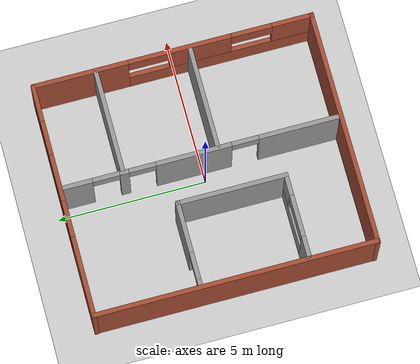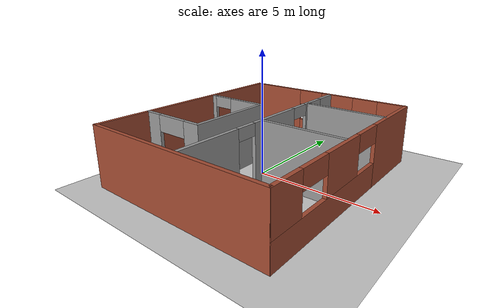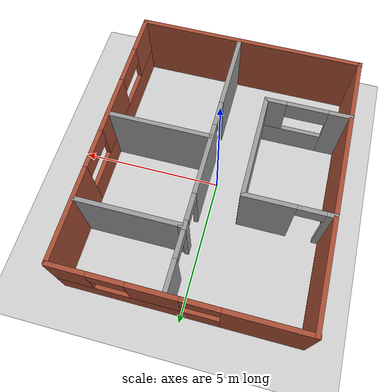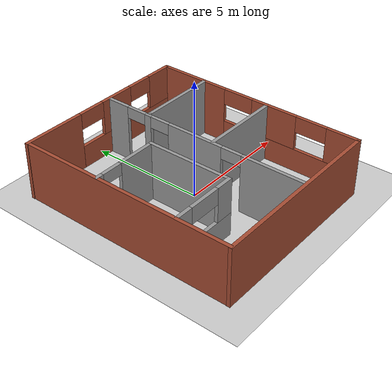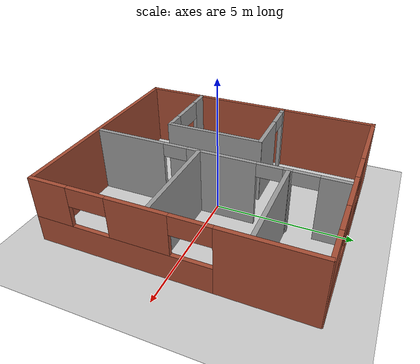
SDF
<?xml version="1.0" encoding="utf-8"?>
<sdf version='1.8'>
  <world name='default'>

    <!-- GUI 뷰포트 설정                                                       -->
    <gui fullscreen='0'>
      <camera name='user_camera'>
        <pose>-9.54285 14.2182 20.3782 -0 0.849795 -1.01702</pose>
        <view_controller>orbit</view_controller>
        <projection_type>perspective</projection_type>
      </camera>
    </gui>

    <!-- Gazebo Harmonic 필수 시스템 플러그인 (world 태그 내부 로드 필수)            -->
    <plugin
      filename="gz-sim-physics-system"
      name="gz::sim::systems::Physics">
    </plugin>
    <plugin
      filename="gz-sim-user-commands-system"
      name="gz::sim::systems::UserCommands">
    </plugin>
    <plugin
      filename="gz-sim-scene-broadcaster-system"
      name="gz::sim::systems::SceneBroadcaster">
    </plugin>
    <plugin
      filename="gz-sim-sensors-system"
      name="gz::sim::systems::Sensors">
      <render_engine>ogre2</render_engine>
    </plugin>

    <!-- 물리 엔진 및 기본 환경 설정                                         -->
    <gravity>0 0 -9.8</gravity>
    <magnetic_field>6e-06 2.3e-05 -4.2e-05</magnetic_field>
    <atmosphere type='adiabatic'/>
    <physics type='ode'>
      <max_step_size>0.001</max_step_size>
      <real_time_factor>1</real_time_factor>
      <real_time_update_rate>1000</real_time_update_rate>
    </physics>
    <scene>
      <ambient>0.4 0.4 0.4 1</ambient>
      <background>0.7 0.7 0.7 1</background>
      <shadows>1</shadows>
    </scene>
    <audio>
      <device>default</device>
    </audio>
    <wind/>
    <spherical_coordinates>
      <surface_model>EARTH_WGS84</surface_model>
      <latitude_deg>0</latitude_deg>
      <longitude_deg>0</longitude_deg>
      <elevation>0</elevation>
      <heading_deg>0</heading_deg>
    </spherical_coordinates>

    <!-- 조명 및 지면 평면                                                   -->
    <light name='sun' type='directional'>
      <cast_shadows>1</cast_shadows>
      <pose>0 0 10 0 -0 0</pose>
      <diffuse>0.8 0.8 0.8 1</diffuse>
      <specular>0.2 0.2 0.2 1</specular>
      <attenuation>
        <range>1000</range>
        <constant>0.9</constant>
        <linear>0.01</linear>
        <quadratic>0.001</quadratic>
      </attenuation>
      <direction>-0.5 0.1 -0.9</direction>
      <spot>
        <inner_angle>0</inner_angle>
        <outer_angle>0</outer_angle>
        <falloff>0</falloff>
      </spot>
    </light>

    <model name='ground_plane'>
      <static>1</static>
      <link name='link'>
        <collision name='collision'>
          <geometry>
            <plane>
              <normal>0 0 1</normal>
              <size>100 100</size>
            </plane>
          </geometry>
          <surface>
            <friction>
              <ode>
                <mu>100</mu>
                <mu2>50</mu2>
              </ode>
              <torsional>
                <ode/>
              </torsional>
            </friction>
            <contact>
              <ode/>
            </contact>
            <bounce/>
          </surface>
          <max_contacts>10</max_contacts>
        </collision>
        <visual name='visual'>
          <cast_shadows>0</cast_shadows>
          <geometry>
            <plane>
              <normal>0 0 1</normal>
              <size>100 100</size>
            </plane>
          </geometry>
          <material>
            <script>
              <uri>file://media/materials/scripts/gazebo.material</uri>
              <name>Gazebo/Grey</name>
            </script>
          </material>
        </visual>
        <self_collide>0</self_collide>
        <enable_wind>0</enable_wind>
        <kinematic>0</kinematic>
      </link>
    </model>

    <!-- 환경 모델 정의 (my_world_example)                                      -->
    <model name='my_world_example'>
      <link name='Wall_14'>
        <pose>0.509968 2.60791 0 0 -0 0</pose>
        <self_collide>0</self_collide>
        <enable_wind>0</enable_wind>
        <kinematic>0</kinematic>
        <visual name='Wall_14_Visual'>
          <pose>0 0 1.25 0 -0 0</pose>
          <geometry>
            <box>
              <size>0.15 0.15 2.5</size>
            </box>
          </geometry>
          <material>
            <script>
              <uri>file://media/materials/scripts/gazebo.material</uri>
              <name>Gazebo/Grey</name>
            </script>
            <ambient>1 1 1 1</ambient>
            <shader type='pixel'/>
          </material>
          <meta>
            <layer>0</layer>
          </meta>
          <transparency>0</transparency>
          <cast_shadows>1</cast_shadows>
        </visual>
        <collision name='Wall_14_Collision'>
          <laser_retro>0</laser_retro>
          <max_contacts>10</max_contacts>
          <pose>0 0 1.25 0 -0 0</pose>
          <geometry>
            <box>
              <size>0.15 0.15 2.5</size>
            </box>
          </geometry>
          <surface>
            <friction>
              <ode>
                <mu>1</mu>
                <mu2>1</mu2>
                <fdir1>0 0 0</fdir1>
                <slip1>0</slip1>
                <slip2>0</slip2>
              </ode>
              <torsional>
                <coefficient>1</coefficient>
                <patch_radius>0</patch_radius>
                <surface_radius>0</surface_radius>
                <use_patch_radius>1</use_patch_radius>
                <ode>
                  <slip>0</slip>
                </ode>
              </torsional>
            </friction>
            <bounce>
              <restitution_coefficient>0</restitution_coefficient>
              <threshold>1e+06</threshold>
            </bounce>
            <contact>
              <collide_without_contact>0</collide_without_contact>
              <collide_without_contact_bitmask>1</collide_without_contact_bitmask>
              <collide_bitmask>1</collide_bitmask>
              <ode>
                <soft_cfm>0</soft_cfm>
                <soft_erp>0.2</soft_erp>
                <kp>1e+13</kp>
                <kd>1</kd>
                <max_vel>0.01</max_vel>
                <min_depth>0</min_depth>
              </ode>
              <bullet>
                <split_impulse>1</split_impulse>
                <split_impulse_penetration_threshold>-0.01</split_impulse_penetration_threshold>
                <soft_cfm>0</soft_cfm>
                <soft_erp>0.2</soft_erp>
                <kp>1e+13</kp>
                <kd>1</kd>
              </bullet>
            </contact>
          </surface>
        </collision>
      </link>
      <link name='Wall_3'>
        <pose>3.93862 -0.015464 0 0 0 -1.5708</pose>
        <self_collide>0</self_collide>
        <enable_wind>0</enable_wind>
        <kinematic>0</kinematic>
        <visual name='Wall_3_Visual_4'>
          <pose>-0.833377 0 2.15 0 -0 0</pose>
          <geometry>
            <box>
              <size>1.378 0.15 0.7</size>
            </box>
          </geometry>
          <material>
            <script>
              <uri>file://media/materials/scripts/gazebo.material</uri>
              <name>Gazebo/Bricks</name>
            </script>
            <ambient>1 1 1 1</ambient>
            <shader type='pixel'/>
          </material>
          <meta>
            <layer>0</layer>
          </meta>
          <transparency>0</transparency>
          <cast_shadows>1</cast_shadows>
        </visual>
        <visual name='Wall_3_Visual_5'>
          <pose>2.64172 0 2.15 0 -0 0</pose>
          <geometry>
            <box>
              <size>1.37 0.15 0.7</size>
            </box>
          </geometry>
          <material>
            <script>
              <uri>file://media/materials/scripts/gazebo.material</uri>
              <name>Gazebo/Bricks</name>
            </script>
            <ambient>1 1 1 1</ambient>
            <shader type='pixel'/>
          </material>
          <meta>
            <layer>0</layer>
          </meta>
          <transparency>0</transparency>
          <cast_shadows>1</cast_shadows>
        </visual>
        <visual name='Wall_3_Visual_3'>
          <pose>4.03836 0 1.75 0 -0 0</pose>
          <geometry>
            <box>
              <size>1.42328 0.15 1.5</size>
            </box>
          </geometry>
          <material>
            <script>
              <uri>file://media/materials/scripts/gazebo.material</uri>
              <name>Gazebo/Bricks</name>
            </script>
            <ambient>1 1 1 1</ambient>
            <shader type='pixel'/>
          </material>
          <meta>
            <layer>0</layer>
          </meta>
          <transparency>0</transparency>
          <cast_shadows>1</cast_shadows>
        </visual>
        <visual name='Wall_3_Visual_1'>
          <pose>1.61381 0 0.5 0 -0 0</pose>
          <geometry>
            <box>
              <size>6.27238 0.15 1</size>
            </box>
          </geometry>
          <material>
            <script>
              <uri>file://media/materials/scripts/gazebo.material</uri>
              <name>Gazebo/Bricks</name>
            </script>
            <ambient>1 1 1 1</ambient>
            <shader type='pixel'/>
          </material>
          <meta>
            <layer>0</layer>
          </meta>
          <transparency>0</transparency>
          <cast_shadows>1</cast_shadows>
        </visual>
        <visual name='Wall_3_Visual_2'>
          <pose>0.90617 0 1.75 0 -0 0</pose>
          <geometry>
            <box>
              <size>2.10109 0.15 1.5</size>
            </box>
          </geometry>
          <material>
            <script>
              <uri>file://media/materials/scripts/gazebo.material</uri>
              <name>Gazebo/Bricks</name>
            </script>
            <ambient>1 1 1 1</ambient>
            <shader type='pixel'/>
          </material>
          <meta>
            <layer>0</layer>
          </meta>
          <transparency>0</transparency>
          <cast_shadows>1</cast_shadows>
        </visual>
        <visual name='Wall_3_Visual_0'>
          <pose>-3.13619 0 1.25 0 -0 0</pose>
          <geometry>
            <box>
              <size>3.22762 0.15 2.5</size>
            </box>
          </geometry>
          <material>
            <script>
              <uri>file://media/materials/scripts/gazebo.material</uri>
              <name>Gazebo/Bricks</name>
            </script>
            <ambient>1 1 1 1</ambient>
            <shader type='pixel'/>
          </material>
          <meta>
            <layer>0</layer>
          </meta>
          <transparency>0</transparency>
          <cast_shadows>1</cast_shadows>
        </visual>
        <collision name='Wall_3_Collision_5'>
          <laser_retro>0</laser_retro>
          <max_contacts>10</max_contacts>
          <pose>2.64172 0 2.15 0 -0 0</pose>
          <geometry>
            <box>
              <size>1.37 0.15 0.7</size>
            </box>
          </geometry>
          <surface>
            <friction>
              <ode>
                <mu>1</mu>
                <mu2>1</mu2>
                <fdir1>0 0 0</fdir1>
                <slip1>0</slip1>
                <slip2>0</slip2>
              </ode>
              <torsional>
                <coefficient>1</coefficient>
                <patch_radius>0</patch_radius>
                <surface_radius>0</surface_radius>
                <use_patch_radius>1</use_patch_radius>
                <ode>
                  <slip>0</slip>
                </ode>
              </torsional>
            </friction>
            <bounce>
              <restitution_coefficient>0</restitution_coefficient>
              <threshold>1e+06</threshold>
            </bounce>
            <contact>
              <collide_without_contact>0</collide_without_contact>
              <collide_without_contact_bitmask>1</collide_without_contact_bitmask>
              <collide_bitmask>1</collide_bitmask>
              <ode>
                <soft_cfm>0</soft_cfm>
                <soft_erp>0.2</soft_erp>
                <kp>1e+13</kp>
                <kd>1</kd>
                <max_vel>0.01</max_vel>
                <min_depth>0</min_depth>
              </ode>
              <bullet>
                <split_impulse>1</split_impulse>
                <split_impulse_penetration_threshold>-0.01</split_impulse_penetration_threshold>
                <soft_cfm>0</soft_cfm>
                <soft_erp>0.2</soft_erp>
                <kp>1e+13</kp>
                <kd>1</kd>
              </bullet>
            </contact>
          </surface>
        </collision>
        <collision name='Wall_3_Collision_2'>
          <laser_retro>0</laser_retro>
          <max_contacts>10</max_contacts>
          <pose>0.90617 0 1.75 0 -0 0</pose>
          <geometry>
            <box>
              <size>2.10109 0.15 1.5</size>
            </box>
          </geometry>
          <surface>
            <friction>
              <ode>
                <mu>1</mu>
                <mu2>1</mu2>
                <fdir1>0 0 0</fdir1>
                <slip1>0</slip1>
                <slip2>0</slip2>
              </ode>
              <torsional>
                <coefficient>1</coefficient>
                <patch_radius>0</patch_radius>
                <surface_radius>0</surface_radius>
                <use_patch_radius>1</use_patch_radius>
                <ode>
                  <slip>0</slip>
                </ode>
              </torsional>
            </friction>
            <bounce>
              <restitution_coefficient>0</restitution_coefficient>
              <threshold>1e+06</threshold>
            </bounce>
            <contact>
              <collide_without_contact>0</collide_without_contact>
              <collide_without_contact_bitmask>1</collide_without_contact_bitmask>
              <collide_bitmask>1</collide_bitmask>
              <ode>
                <soft_cfm>0</soft_cfm>
                <soft_erp>0.2</soft_erp>
                <kp>1e+13</kp>
                <kd>1</kd>
                <max_vel>0.01</max_vel>
                <min_depth>0</min_depth>
              </ode>
              <bullet>
                <split_impulse>1</split_impulse>
                <split_impulse_penetration_threshold>-0.01</split_impulse_penetration_threshold>
                <soft_cfm>0</soft_cfm>
                <soft_erp>0.2</soft_erp>
                <kp>1e+13</kp>
                <kd>1</kd>
              </bullet>
            </contact>
          </surface>
        </collision>
        <collision name='Wall_3_Collision_4'>
          <laser_retro>0</laser_retro>
          <max_contacts>10</max_contacts>
          <pose>-0.833377 0 2.15 0 -0 0</pose>
          <geometry>
            <box>
              <size>1.378 0.15 0.7</size>
            </box>
          </geometry>
          <surface>
            <friction>
              <ode>
                <mu>1</mu>
                <mu2>1</mu2>
                <fdir1>0 0 0</fdir1>
                <slip1>0</slip1>
                <slip2>0</slip2>
              </ode>
              <torsional>
                <coefficient>1</coefficient>
                <patch_radius>0</patch_radius>
                <surface_radius>0</surface_radius>
                <use_patch_radius>1</use_patch_radius>
                <ode>
                  <slip>0</slip>
                </ode>
              </torsional>
            </friction>
            <bounce>
              <restitution_coefficient>0</restitution_coefficient>
              <threshold>1e+06</threshold>
            </bounce>
            <contact>
              <collide_without_contact>0</collide_without_contact>
              <collide_without_contact_bitmask>1</collide_without_contact_bitmask>
              <collide_bitmask>1</collide_bitmask>
              <ode>
                <soft_cfm>0</soft_cfm>
                <soft_erp>0.2</soft_erp>
                <kp>1e+13</kp>
                <kd>1</kd>
                <max_vel>0.01</max_vel>
                <min_depth>0</min_depth>
              </ode>
              <bullet>
                <split_impulse>1</split_impulse>
                <split_impulse_penetration_threshold>-0.01</split_impulse_penetration_threshold>
                <soft_cfm>0</soft_cfm>
                <soft_erp>0.2</soft_erp>
                <kp>1e+13</kp>
                <kd>1</kd>
              </bullet>
            </contact>
          </surface>
        </collision>
        <collision name='Wall_3_Collision_3'>
          <laser_retro>0</laser_retro>
          <max_contacts>10</max_contacts>
          <pose>4.03836 0 1.75 0 -0 0</pose>
          <geometry>
            <box>
              <size>1.42328 0.15 1.5</size>
            </box>
          </geometry>
          <surface>
            <friction>
              <ode>
                <mu>1</mu>
                <mu2>1</mu2>
                <fdir1>0 0 0</fdir1>
                <slip1>0</slip1>
                <slip2>0</slip2>
              </ode>
              <torsional>
                <coefficient>1</coefficient>
                <patch_radius>0</patch_radius>
                <surface_radius>0</surface_radius>
                <use_patch_radius>1</use_patch_radius>
                <ode>
                  <slip>0</slip>
                </ode>
              </torsional>
            </friction>
            <bounce>
              <restitution_coefficient>0</restitution_coefficient>
              <threshold>1e+06</threshold>
            </bounce>
            <contact>
              <collide_without_contact>0</collide_without_contact>
              <collide_without_contact_bitmask>1</collide_without_contact_bitmask>
              <collide_bitmask>1</collide_bitmask>
              <ode>
                <soft_cfm>0</soft_cfm>
                <soft_erp>0.2</soft_erp>
                <kp>1e+13</kp>
                <kd>1</kd>
                <max_vel>0.01</max_vel>
                <min_depth>0</min_depth>
              </ode>
              <bullet>
                <split_impulse>1</split_impulse>
                <split_impulse_penetration_threshold>-0.01</split_impulse_penetration_threshold>
                <soft_cfm>0</soft_cfm>
                <soft_erp>0.2</soft_erp>
                <kp>1e+13</kp>
                <kd>1</kd>
              </bullet>
            </contact>
          </surface>
        </collision>
        <collision name='Wall_3_Collision_1'>
          <laser_retro>0</laser_retro>
          <max_contacts>10</max_contacts>
          <pose>1.61381 0 0.5 0 -0 0</pose>
          <geometry>
            <box>
              <size>6.27238 0.15 1</size>
            </box>
          </geometry>
          <surface>
            <friction>
              <ode>
                <mu>1</mu>
                <mu2>1</mu2>
                <fdir1>0 0 0</fdir1>
                <slip1>0</slip1>
                <slip2>0</slip2>
              </ode>
              <torsional>
                <coefficient>1</coefficient>
                <patch_radius>0</patch_radius>
                <surface_radius>0</surface_radius>
                <use_patch_radius>1</use_patch_radius>
                <ode>
                  <slip>0</slip>
                </ode>
              </torsional>
            </friction>
            <bounce>
              <restitution_coefficient>0</restitution_coefficient>
              <threshold>1e+06</threshold>
            </bounce>
            <contact>
              <collide_without_contact>0</collide_without_contact>
              <collide_without_contact_bitmask>1</collide_without_contact_bitmask>
              <collide_bitmask>1</collide_bitmask>
              <ode>
                <soft_cfm>0</soft_cfm>
                <soft_erp>0.2</soft_erp>
                <kp>1e+13</kp>
                <kd>1</kd>
                <max_vel>0.01</max_vel>
                <min_depth>0</min_depth>
              </ode>
              <bullet>
                <split_impulse>1</split_impulse>
                <split_impulse_penetration_threshold>-0.01</split_impulse_penetration_threshold>
                <soft_cfm>0</soft_cfm>
                <soft_erp>0.2</soft_erp>
                <kp>1e+13</kp>
                <kd>1</kd>
              </bullet>
            </contact>
          </surface>
        </collision>
        <collision name='Wall_3_Collision_0'>
          <laser_retro>0</laser_retro>
          <max_contacts>10</max_contacts>
          <pose>-3.13619 0 1.25 0 -0 0</pose>
          <geometry>
            <box>
              <size>3.22762 0.15 2.5</size>
            </box>
          </geometry>
          <surface>
            <friction>
              <ode>
                <mu>1</mu>
                <mu2>1</mu2>
                <fdir1>0 0 0</fdir1>
                <slip1>0</slip1>
                <slip2>0</slip2>
              </ode>
              <torsional>
                <coefficient>1</coefficient>
                <patch_radius>0</patch_radius>
                <surface_radius>0</surface_radius>
                <use_patch_radius>1</use_patch_radius>
                <ode>
                  <slip>0</slip>
                </ode>
              </torsional>
            </friction>
            <bounce>
              <restitution_coefficient>0</restitution_coefficient>
              <threshold>1e+06</threshold>
            </bounce>
            <contact>
              <collide_without_contact>0</collide_without_contact>
              <collide_without_contact_bitmask>1</collide_without_contact_bitmask>
              <collide_bitmask>1</collide_bitmask>
              <ode>
                <soft_cfm>0</soft_cfm>
                <soft_erp>0.2</soft_erp>
                <kp>1e+13</kp>
                <kd>1</kd>
                <max_vel>0.01</max_vel>
                <min_depth>0</min_depth>
              </ode>
              <bullet>
                <split_impulse>1</split_impulse>
                <split_impulse_penetration_threshold>-0.01</split_impulse_penetration_threshold>
                <soft_cfm>0</soft_cfm>
                <soft_erp>0.2</soft_erp>
                <kp>1e+13</kp>
                <kd>1</kd>
              </bullet>
            </contact>
          </surface>
        </collision>
      </link>
      <link name='Wall_33'>
        <pose>-3.92017 0.013616 0 0 0 -1.5708</pose>
        <self_collide>0</self_collide>
        <enable_wind>0</enable_wind>
        <kinematic>0</kinematic>
        <visual name='Wall_33_Visual'>
          <pose>0 0 1.25 0 -0 0</pose>
          <geometry>
            <box>
              <size>9.5 0.15 2.5</size>
            </box>
          </geometry>
          <material>
            <script>
              <uri>file://media/materials/scripts/gazebo.material</uri>
              <name>Gazebo/Bricks</name>
            </script>
            <ambient>1 1 1 1</ambient>
            <shader type='pixel'/>
          </material>
          <meta>
            <layer>0</layer>
          </meta>
          <transparency>0</transparency>
          <cast_shadows>1</cast_shadows>
        </visual>
        <collision name='Wall_33_Collision'>
          <laser_retro>0</laser_retro>
          <max_contacts>10</max_contacts>
          <pose>0 0 1.25 0 -0 0</pose>
          <geometry>
            <box>
              <size>9.5 0.15 2.5</size>
            </box>
          </geometry>
          <surface>
            <friction>
              <ode>
                <mu>1</mu>
                <mu2>1</mu2>
                <fdir1>0 0 0</fdir1>
                <slip1>0</slip1>
                <slip2>0</slip2>
              </ode>
              <torsional>
                <coefficient>1</coefficient>
                <patch_radius>0</patch_radius>
                <surface_radius>0</surface_radius>
                <use_patch_radius>1</use_patch_radius>
                <ode>
                  <slip>0</slip>
                </ode>
              </torsional>
            </friction>
            <bounce>
              <restitution_coefficient>0</restitution_coefficient>
              <threshold>1e+06</threshold>
            </bounce>
            <contact>
              <collide_without_contact>0</collide_without_contact>
              <collide_without_contact_bitmask>1</collide_without_contact_bitmask>
              <collide_bitmask>1</collide_bitmask>
              <ode>
                <soft_cfm>0</soft_cfm>
                <soft_erp>0.2</soft_erp>
                <kp>1e+13</kp>
                <kd>1</kd>
                <max_vel>0.01</max_vel>
                <min_depth>0</min_depth>
              </ode>
              <bullet>
                <split_impulse>1</split_impulse>
                <split_impulse_penetration_threshold>-0.01</split_impulse_penetration_threshold>
                <soft_cfm>0</soft_cfm>
                <soft_erp>0.2</soft_erp>
                <kp>1e+13</kp>
                <kd>1</kd>
              </bullet>
            </contact>
          </surface>
        </collision>
      </link>
      <link name='Wall_35'>
        <pose>-2.48639 1.16661 0 0 -0 0</pose>
        <self_collide>0</self_collide>
        <enable_wind>0</enable_wind>
        <kinematic>0</kinematic>
        <visual name='Wall_35_Visual_1'>
          <pose>0.62567 0 1.25 0 -0 0</pose>
          <geometry>
            <box>
              <size>1.74866 0.15 2.5</size>
            </box>
          </geometry>
          <material>
            <script>
              <uri>file://media/materials/scripts/gazebo.material</uri>
              <name>Gazebo/Grey</name>
            </script>
            <ambient>1 1 1 1</ambient>
            <shader type='pixel'/>
          </material>
          <meta>
            <layer>0</layer>
          </meta>
          <transparency>0</transparency>
          <cast_shadows>1</cast_shadows>
        </visual>
        <visual name='Wall_35_Visual_0'>
          <pose>-1.32433 0 1.25 0 -0 0</pose>
          <geometry>
            <box>
              <size>0.35134 0.15 2.5</size>
            </box>
          </geometry>
          <material>
            <script>
              <uri>file://media/materials/scripts/gazebo.material</uri>
              <name>Gazebo/Grey</name>
            </script>
            <ambient>1 1 1 1</ambient>
            <shader type='pixel'/>
          </material>
          <meta>
            <layer>0</layer>
          </meta>
          <transparency>0</transparency>
          <cast_shadows>1</cast_shadows>
        </visual>
        <visual name='Wall_35_Visual_2'>
          <pose>-0.69866 0 2.25 0 -0 0</pose>
          <geometry>
            <box>
              <size>0.9 0.15 0.5</size>
            </box>
          </geometry>
          <material>
            <script>
              <uri>file://media/materials/scripts/gazebo.material</uri>
              <name>Gazebo/Grey</name>
            </script>
            <ambient>1 1 1 1</ambient>
            <shader type='pixel'/>
          </material>
          <meta>
            <layer>0</layer>
          </meta>
          <transparency>0</transparency>
          <cast_shadows>1</cast_shadows>
        </visual>
        <collision name='Wall_35_Collision_0'>
          <laser_retro>0</laser_retro>
          <max_contacts>10</max_contacts>
          <pose>-1.32433 0 1.25 0 -0 0</pose>
          <geometry>
            <box>
              <size>0.35134 0.15 2.5</size>
            </box>
          </geometry>
          <surface>
            <friction>
              <ode>
                <mu>1</mu>
                <mu2>1</mu2>
                <fdir1>0 0 0</fdir1>
                <slip1>0</slip1>
                <slip2>0</slip2>
              </ode>
              <torsional>
                <coefficient>1</coefficient>
                <patch_radius>0</patch_radius>
                <surface_radius>0</surface_radius>
                <use_patch_radius>1</use_patch_radius>
                <ode>
                  <slip>0</slip>
                </ode>
              </torsional>
            </friction>
            <bounce>
              <restitution_coefficient>0</restitution_coefficient>
              <threshold>1e+06</threshold>
            </bounce>
            <contact>
              <collide_without_contact>0</collide_without_contact>
              <collide_without_contact_bitmask>1</collide_without_contact_bitmask>
              <collide_bitmask>1</collide_bitmask>
              <ode>
                <soft_cfm>0</soft_cfm>
                <soft_erp>0.2</soft_erp>
                <kp>1e+13</kp>
                <kd>1</kd>
                <max_vel>0.01</max_vel>
                <min_depth>0</min_depth>
              </ode>
              <bullet>
                <split_impulse>1</split_impulse>
                <split_impulse_penetration_threshold>-0.01</split_impulse_penetration_threshold>
                <soft_cfm>0</soft_cfm>
                <soft_erp>0.2</soft_erp>
                <kp>1e+13</kp>
                <kd>1</kd>
              </bullet>
            </contact>
          </surface>
        </collision>
        <collision name='Wall_35_Collision_2'>
          <laser_retro>0</laser_retro>
          <max_contacts>10</max_contacts>
          <pose>-0.69866 0 2.25 0 -0 0</pose>
          <geometry>
            <box>
              <size>0.9 0.15 0.5</size>
            </box>
          </geometry>
          <surface>
            <friction>
              <ode>
                <mu>1</mu>
                <mu2>1</mu2>
                <fdir1>0 0 0</fdir1>
                <slip1>0</slip1>
                <slip2>0</slip2>
              </ode>
              <torsional>
                <coefficient>1</coefficient>
                <patch_radius>0</patch_radius>
                <surface_radius>0</surface_radius>
                <use_patch_radius>1</use_patch_radius>
                <ode>
                  <slip>0</slip>
                </ode>
              </torsional>
            </friction>
            <bounce>
              <restitution_coefficient>0</restitution_coefficient>
              <threshold>1e+06</threshold>
            </bounce>
            <contact>
              <collide_without_contact>0</collide_without_contact>
              <collide_without_contact_bitmask>1</collide_without_contact_bitmask>
              <collide_bitmask>1</collide_bitmask>
              <ode>
                <soft_cfm>0</soft_cfm>
                <soft_erp>0.2</soft_erp>
                <kp>1e+13</kp>
                <kd>1</kd>
                <max_vel>0.01</max_vel>
                <min_depth>0</min_depth>
              </ode>
              <bullet>
                <split_impulse>1</split_impulse>
                <split_impulse_penetration_threshold>-0.01</split_impulse_penetration_threshold>
                <soft_cfm>0</soft_cfm>
                <soft_erp>0.2</soft_erp>
                <kp>1e+13</kp>
                <kd>1</kd>
              </bullet>
            </contact>
          </surface>
        </collision>
        <collision name='Wall_35_Collision_1'>
          <laser_retro>0</laser_retro>
          <max_contacts>10</max_contacts>
          <pose>0.62567 0 1.25 0 -0 0</pose>
          <geometry>
            <box>
              <size>1.74866 0.15 2.5</size>
            </box>
          </geometry>
          <surface>
            <friction>
              <ode>
                <mu>1</mu>
                <mu2>1</mu2>
                <fdir1>0 0 0</fdir1>
                <slip1>0</slip1>
                <slip2>0</slip2>
              </ode>
              <torsional>
                <coefficient>1</coefficient>
                <patch_radius>0</patch_radius>
                <surface_radius>0</surface_radius>
                <use_patch_radius>1</use_patch_radius>
                <ode>
                  <slip>0</slip>
                </ode>
              </torsional>
            </friction>
            <bounce>
              <restitution_coefficient>0</restitution_coefficient>
              <threshold>1e+06</threshold>
            </bounce>
            <contact>
              <collide_without_contact>0</collide_without_contact>
              <collide_without_contact_bitmask>1</collide_without_contact_bitmask>
              <collide_bitmask>1</collide_bitmask>
              <ode>
                <soft_cfm>0</soft_cfm>
                <soft_erp>0.2</soft_erp>
                <kp>1e+13</kp>
                <kd>1</kd>
                <max_vel>0.01</max_vel>
                <min_depth>0</min_depth>
              </ode>
              <bullet>
                <split_impulse>1</split_impulse>
                <split_impulse_penetration_threshold>-0.01</split_impulse_penetration_threshold>
                <soft_cfm>0</soft_cfm>
                <soft_erp>0.2</soft_erp>
                <kp>1e+13</kp>
                <kd>1</kd>
              </bullet>
            </contact>
          </surface>
        </collision>
      </link>
      <link name='Wall_38'>
        <pose>-0.013622 4.69452 0 0 -0 0</pose>
        <self_collide>0</self_collide>
        <enable_wind>0</enable_wind>
        <kinematic>0</kinematic>
        <visual name='Wall_38_Visual_4'>
          <pose>-0.631709 0 2.15 0 -0 0</pose>
          <geometry>
            <box>
              <size>1.221 0.15 0.7</size>
            </box>
          </geometry>
          <material>
            <script>
              <uri>file://media/materials/scripts/gazebo.material</uri>
              <name>Gazebo/Bricks</name>
            </script>
            <ambient>1 1 1 1</ambient>
            <shader type='pixel'/>
          </material>
          <meta>
            <layer>0</layer>
          </meta>
          <transparency>0</transparency>
          <cast_shadows>1</cast_shadows>
        </visual>
        <visual name='Wall_38_Visual_5'>
          <pose>2.15803 0 2.15 0 -0 0</pose>
          <geometry>
            <box>
              <size>1.163 0.15 0.7</size>
            </box>
          </geometry>
          <material>
            <script>
              <uri>file://media/materials/scripts/gazebo.material</uri>
              <name>Gazebo/Bricks</name>
            </script>
            <ambient>1 1 1 1</ambient>
            <shader type='pixel'/>
          </material>
          <meta>
            <layer>0</layer>
          </meta>
          <transparency>0</transparency>
          <cast_shadows>1</cast_shadows>
        </visual>
        <visual name='Wall_38_Visual_1'>
          <pose>1.3789 0 0.5 0 -0 0</pose>
          <geometry>
            <box>
              <size>5.24221 0.15 1</size>
            </box>
          </geometry>
          <material>
            <script>
              <uri>file://media/materials/scripts/gazebo.material</uri>
              <name>Gazebo/Bricks</name>
            </script>
            <ambient>1 1 1 1</ambient>
            <shader type='pixel'/>
          </material>
          <meta>
            <layer>0</layer>
          </meta>
          <transparency>0</transparency>
          <cast_shadows>1</cast_shadows>
        </visual>
        <visual name='Wall_38_Visual_2'>
          <pose>0.777661 0 1.75 0 -0 0</pose>
          <geometry>
            <box>
              <size>1.59774 0.15 1.5</size>
            </box>
          </geometry>
          <material>
            <script>
              <uri>file://media/materials/scripts/gazebo.material</uri>
              <name>Gazebo/Bricks</name>
            </script>
            <ambient>1 1 1 1</ambient>
            <shader type='pixel'/>
          </material>
          <meta>
            <layer>0</layer>
          </meta>
          <transparency>0</transparency>
          <cast_shadows>1</cast_shadows>
        </visual>
        <visual name='Wall_38_Visual_3'>
          <pose>3.36977 0 1.75 0 -0 0</pose>
          <geometry>
            <box>
              <size>1.26047 0.15 1.5</size>
            </box>
          </geometry>
          <material>
            <script>
              <uri>file://media/materials/scripts/gazebo.material</uri>
              <name>Gazebo/Bricks</name>
            </script>
            <ambient>1 1 1 1</ambient>
            <shader type='pixel'/>
          </material>
          <meta>
            <layer>0</layer>
          </meta>
          <transparency>0</transparency>
          <cast_shadows>1</cast_shadows>
        </visual>
        <visual name='Wall_38_Visual_0'>
          <pose>-2.6211 0 1.25 0 -0 0</pose>
          <geometry>
            <box>
              <size>2.75779 0.15 2.5</size>
            </box>
          </geometry>
          <material>
            <script>
              <uri>file://media/materials/scripts/gazebo.material</uri>
              <name>Gazebo/Bricks</name>
            </script>
            <ambient>1 1 1 1</ambient>
            <shader type='pixel'/>
          </material>
          <meta>
            <layer>0</layer>
          </meta>
          <transparency>0</transparency>
          <cast_shadows>1</cast_shadows>
        </visual>
        <collision name='Wall_38_Collision_4'>
          <laser_retro>0</laser_retro>
          <max_contacts>10</max_contacts>
          <pose>-0.631709 0 2.15 0 -0 0</pose>
          <geometry>
            <box>
              <size>1.221 0.15 0.7</size>
            </box>
          </geometry>
          <surface>
            <friction>
              <ode>
                <mu>1</mu>
                <mu2>1</mu2>
                <fdir1>0 0 0</fdir1>
                <slip1>0</slip1>
                <slip2>0</slip2>
              </ode>
              <torsional>
                <coefficient>1</coefficient>
                <patch_radius>0</patch_radius>
                <surface_radius>0</surface_radius>
                <use_patch_radius>1</use_patch_radius>
                <ode>
                  <slip>0</slip>
                </ode>
              </torsional>
            </friction>
            <bounce>
              <restitution_coefficient>0</restitution_coefficient>
              <threshold>1e+06</threshold>
            </bounce>
            <contact>
              <collide_without_contact>0</collide_without_contact>
              <collide_without_contact_bitmask>1</collide_without_contact_bitmask>
              <collide_bitmask>1</collide_bitmask>
              <ode>
                <soft_cfm>0</soft_cfm>
                <soft_erp>0.2</soft_erp>
                <kp>1e+13</kp>
                <kd>1</kd>
                <max_vel>0.01</max_vel>
                <min_depth>0</min_depth>
              </ode>
              <bullet>
                <split_impulse>1</split_impulse>
                <split_impulse_penetration_threshold>-0.01</split_impulse_penetration_threshold>
                <soft_cfm>0</soft_cfm>
                <soft_erp>0.2</soft_erp>
                <kp>1e+13</kp>
                <kd>1</kd>
              </bullet>
            </contact>
          </surface>
        </collision>
        <collision name='Wall_38_Collision_2'>
          <laser_retro>0</laser_retro>
          <max_contacts>10</max_contacts>
          <pose>0.777661 0 1.75 0 -0 0</pose>
          <geometry>
            <box>
              <size>1.59774 0.15 1.5</size>
            </box>
          </geometry>
          <surface>
            <friction>
              <ode>
                <mu>1</mu>
                <mu2>1</mu2>
                <fdir1>0 0 0</fdir1>
                <slip1>0</slip1>
                <slip2>0</slip2>
              </ode>
              <torsional>
                <coefficient>1</coefficient>
                <patch_radius>0</patch_radius>
                <surface_radius>0</surface_radius>
                <use_patch_radius>1</use_patch_radius>
                <ode>
                  <slip>0</slip>
                </ode>
              </torsional>
            </friction>
            <bounce>
              <restitution_coefficient>0</restitution_coefficient>
              <threshold>1e+06</threshold>
            </bounce>
            <contact>
              <collide_without_contact>0</collide_without_contact>
              <collide_without_contact_bitmask>1</collide_without_contact_bitmask>
              <collide_bitmask>1</collide_bitmask>
              <ode>
                <soft_cfm>0</soft_cfm>
                <soft_erp>0.2</soft_erp>
                <kp>1e+13</kp>
                <kd>1</kd>
                <max_vel>0.01</max_vel>
                <min_depth>0</min_depth>
              </ode>
              <bullet>
                <split_impulse>1</split_impulse>
                <split_impulse_penetration_threshold>-0.01</split_impulse_penetration_threshold>
                <soft_cfm>0</soft_cfm>
                <soft_erp>0.2</soft_erp>
                <kp>1e+13</kp>
                <kd>1</kd>
              </bullet>
            </contact>
          </surface>
        </collision>
        <collision name='Wall_38_Collision_1'>
          <laser_retro>0</laser_retro>
          <max_contacts>10</max_contacts>
          <pose>1.3789 0 0.5 0 -0 0</pose>
          <geometry>
            <box>
              <size>5.24221 0.15 1</size>
            </box>
          </geometry>
          <surface>
            <friction>
              <ode>
                <mu>1</mu>
                <mu2>1</mu2>
                <fdir1>0 0 0</fdir1>
                <slip1>0</slip1>
                <slip2>0</slip2>
              </ode>
              <torsional>
                <coefficient>1</coefficient>
                <patch_radius>0</patch_radius>
                <surface_radius>0</surface_radius>
                <use_patch_radius>1</use_patch_radius>
                <ode>
                  <slip>0</slip>
                </ode>
              </torsional>
            </friction>
            <bounce>
              <restitution_coefficient>0</restitution_coefficient>
              <threshold>1e+06</threshold>
            </bounce>
            <contact>
              <collide_without_contact>0</collide_without_contact>
              <collide_without_contact_bitmask>1</collide_without_contact_bitmask>
              <collide_bitmask>1</collide_bitmask>
              <ode>
                <soft_cfm>0</soft_cfm>
                <soft_erp>0.2</soft_erp>
                <kp>1e+13</kp>
                <kd>1</kd>
                <max_vel>0.01</max_vel>
                <min_depth>0</min_depth>
              </ode>
              <bullet>
                <split_impulse>1</split_impulse>
                <split_impulse_penetration_threshold>-0.01</split_impulse_penetration_threshold>
                <soft_cfm>0</soft_cfm>
                <soft_erp>0.2</soft_erp>
                <kp>1e+13</kp>
                <kd>1</kd>
              </bullet>
            </contact>
          </surface>
        </collision>
        <collision name='Wall_38_Collision_5'>
          <laser_retro>0</laser_retro>
          <max_contacts>10</max_contacts>
          <pose>2.15803 0 2.15 0 -0 0</pose>
          <geometry>
            <box>
              <size>1.163 0.15 0.7</size>
            </box>
          </geometry>
          <surface>
            <friction>
              <ode>
                <mu>1</mu>
                <mu2>1</mu2>
                <fdir1>0 0 0</fdir1>
                <slip1>0</slip1>
                <slip2>0</slip2>
              </ode>
              <torsional>
                <coefficient>1</coefficient>
                <patch_radius>0</patch_radius>
                <surface_radius>0</surface_radius>
                <use_patch_radius>1</use_patch_radius>
                <ode>
                  <slip>0</slip>
                </ode>
              </torsional>
            </friction>
            <bounce>
              <restitution_coefficient>0</restitution_coefficient>
              <threshold>1e+06</threshold>
            </bounce>
            <contact>
              <collide_without_contact>0</collide_without_contact>
              <collide_without_contact_bitmask>1</collide_without_contact_bitmask>
              <collide_bitmask>1</collide_bitmask>
              <ode>
                <soft_cfm>0</soft_cfm>
                <soft_erp>0.2</soft_erp>
                <kp>1e+13</kp>
                <kd>1</kd>
                <max_vel>0.01</max_vel>
                <min_depth>0</min_depth>
              </ode>
              <bullet>
                <split_impulse>1</split_impulse>
                <split_impulse_penetration_threshold>-0.01</split_impulse_penetration_threshold>
                <soft_cfm>0</soft_cfm>
                <soft_erp>0.2</soft_erp>
                <kp>1e+13</kp>
                <kd>1</kd>
              </bullet>
            </contact>
          </surface>
        </collision>
        <collision name='Wall_38_Collision_3'>
          <laser_retro>0</laser_retro>
          <max_contacts>10</max_contacts>
          <pose>3.36977 0 1.75 0 -0 0</pose>
          <geometry>
            <box>
              <size>1.26047 0.15 1.5</size>
            </box>
          </geometry>
          <surface>
            <friction>
              <ode>
                <mu>1</mu>
                <mu2>1</mu2>
                <fdir1>0 0 0</fdir1>
                <slip1>0</slip1>
                <slip2>0</slip2>
              </ode>
              <torsional>
                <coefficient>1</coefficient>
                <patch_radius>0</patch_radius>
                <surface_radius>0</surface_radius>
                <use_patch_radius>1</use_patch_radius>
                <ode>
                  <slip>0</slip>
                </ode>
              </torsional>
            </friction>
            <bounce>
              <restitution_coefficient>0</restitution_coefficient>
              <threshold>1e+06</threshold>
            </bounce>
            <contact>
              <collide_without_contact>0</collide_without_contact>
              <collide_without_contact_bitmask>1</collide_without_contact_bitmask>
              <collide_bitmask>1</collide_bitmask>
              <ode>
                <soft_cfm>0</soft_cfm>
                <soft_erp>0.2</soft_erp>
                <kp>1e+13</kp>
                <kd>1</kd>
                <max_vel>0.01</max_vel>
                <min_depth>0</min_depth>
              </ode>
              <bullet>
                <split_impulse>1</split_impulse>
                <split_impulse_penetration_threshold>-0.01</split_impulse_penetration_threshold>
                <soft_cfm>0</soft_cfm>
                <soft_erp>0.2</soft_erp>
                <kp>1e+13</kp>
                <kd>1</kd>
              </bullet>
            </contact>
          </surface>
        </collision>
        <collision name='Wall_38_Collision_0'>
          <laser_retro>0</laser_retro>
          <max_contacts>10</max_contacts>
          <pose>-2.6211 0 1.25 0 -0 0</pose>
          <geometry>
            <box>
              <size>2.75779 0.15 2.5</size>
            </box>
          </geometry>
          <surface>
            <friction>
              <ode>
                <mu>1</mu>
                <mu2>1</mu2>
                <fdir1>0 0 0</fdir1>
                <slip1>0</slip1>
                <slip2>0</slip2>
              </ode>
              <torsional>
                <coefficient>1</coefficient>
                <patch_radius>0</patch_radius>
                <surface_radius>0</surface_radius>
                <use_patch_radius>1</use_patch_radius>
                <ode>
                  <slip>0</slip>
                </ode>
              </torsional>
            </friction>
            <bounce>
              <restitution_coefficient>0</restitution_coefficient>
              <threshold>1e+06</threshold>
            </bounce>
            <contact>
              <collide_without_contact>0</collide_without_contact>
              <collide_without_contact_bitmask>1</collide_without_contact_bitmask>
              <collide_bitmask>1</collide_bitmask>
              <ode>
                <soft_cfm>0</soft_cfm>
                <soft_erp>0.2</soft_erp>
                <kp>1e+13</kp>
                <kd>1</kd>
                <max_vel>0.01</max_vel>
                <min_depth>0</min_depth>
              </ode>
              <bullet>
                <split_impulse>1</split_impulse>
                <split_impulse_penetration_threshold>-0.01</split_impulse_penetration_threshold>
                <soft_cfm>0</soft_cfm>
                <soft_erp>0.2</soft_erp>
                <kp>1e+13</kp>
                <kd>1</kd>
              </bullet>
            </contact>
          </surface>
        </collision>
      </link>
      <link name='Wall_42'>
        <pose>0.387902 0.000987 0 0 0 -1.5708</pose>
        <self_collide>0</self_collide>
        <enable_wind>0</enable_wind>
        <kinematic>0</kinematic>
        <gravity>1</gravity>
        <inertial>
          <mass>1</mass>
          <pose>0 0 0 0 -0 0</pose>
          <inertia>
            <ixx>1</ixx>
            <ixy>0</ixy>
            <ixz>0</ixz>
            <iyy>1</iyy>
            <iyz>0</iyz>
            <izz>1</izz>
          </inertia>
        </inertial>
        <visual name='Wall_42_Visual_0'>
          <pose>-4.12408 0 1.25 0 -0 0</pose>
          <geometry>
            <box>
              <size>1.00184 0.15 2.5</size>
            </box>
          </geometry>
          <material>
            <script>
              <uri>file://media/materials/scripts/gazebo.material</uri>
              <name>Gazebo/Grey</name>
            </script>
            <ambient>1 1 1 1</ambient>
            <shader type='pixel'>
              <normal_map>__default__</normal_map>
            </shader>
          </material>
          <meta>
            <layer>0</layer>
          </meta>
          <transparency>0</transparency>
          <cast_shadows>1</cast_shadows>
        </visual>
        <visual name='Wall_42_Visual_1'>
          <pose>-2.5695 0 1.25 0 -0 0</pose>
          <geometry>
            <box>
              <size>0.307325 0.15 2.5</size>
            </box>
          </geometry>
          <material>
            <script>
              <uri>file://media/materials/scripts/gazebo.material</uri>
              <name>Gazebo/Grey</name>
            </script>
            <ambient>1 1 1 1</ambient>
            <shader type='pixel'>
              <normal_map>__default__</normal_map>
            </shader>
          </material>
          <meta>
            <layer>0</layer>
          </meta>
          <transparency>0</transparency>
          <cast_shadows>1</cast_shadows>
        </visual>
        <visual name='Wall_42_Visual_4'>
          <pose>-3.17316 0 2.25 0 -0 0</pose>
          <geometry>
            <box>
              <size>0.9 0.15 0.5</size>
            </box>
          </geometry>
          <material>
            <script>
              <uri>file://media/materials/scripts/gazebo.material</uri>
              <name>Gazebo/Grey</name>
            </script>
            <ambient>1 1 1 1</ambient>
            <shader type='pixel'>
              <normal_map>__default__</normal_map>
            </shader>
          </material>
          <meta>
            <layer>0</layer>
          </meta>
          <transparency>0</transparency>
          <cast_shadows>1</cast_shadows>
        </visual>
        <visual name='Wall_42_Visual_5'>
          <pose>-1.96584 0 2.25 0 -0 0</pose>
          <geometry>
            <box>
              <size>0.9 0.15 0.5</size>
            </box>
          </geometry>
          <material>
            <script>
              <uri>file://media/materials/scripts/gazebo.material</uri>
              <name>Gazebo/Grey</name>
            </script>
            <ambient>1 1 1 1</ambient>
            <shader type='pixel'>
              <normal_map>__default__</normal_map>
            </shader>
          </material>
          <meta>
            <layer>0</layer>
          </meta>
          <transparency>0</transparency>
          <cast_shadows>1</cast_shadows>
        </visual>
        <visual name='Wall_42_Visual_6'>
          <pose>1.47532 0 2.25 0 -0 0</pose>
          <geometry>
            <box>
              <size>0.9 0.15 0.5</size>
            </box>
          </geometry>
          <material>
            <script>
              <uri>file://media/materials/scripts/gazebo.material</uri>
              <name>Gazebo/Grey</name>
            </script>
            <ambient>1 1 1 1</ambient>
            <shader type='pixel'>
              <normal_map>__default__</normal_map>
            </shader>
          </material>
          <meta>
            <layer>0</layer>
          </meta>
          <transparency>0</transparency>
          <cast_shadows>1</cast_shadows>
        </visual>
        <visual name='Wall_42_Visual_3'>
          <pose>3.27516 0 1.25 0 -0 0</pose>
          <geometry>
            <box>
              <size>2.69968 0.15 2.5</size>
            </box>
          </geometry>
          <material>
            <script>
              <uri>file://media/materials/scripts/gazebo.material</uri>
              <name>Gazebo/Grey</name>
            </script>
            <ambient>1 1 1 1</ambient>
            <shader type='pixel'>
              <normal_map>__default__</normal_map>
            </shader>
          </material>
          <meta>
            <layer>0</layer>
          </meta>
          <transparency>0</transparency>
          <cast_shadows>1</cast_shadows>
        </visual>
        <visual name='Wall_42_Visual_2'>
          <pose>-0.245259 0 1.25 0 -0 0</pose>
          <geometry>
            <box>
              <size>2.54116 0.15 2.5</size>
            </box>
          </geometry>
          <material>
            <script>
              <uri>file://media/materials/scripts/gazebo.material</uri>
              <name>Gazebo/Grey</name>
            </script>
            <ambient>1 1 1 1</ambient>
            <shader type='pixel'>
              <normal_map>__default__</normal_map>
            </shader>
          </material>
          <meta>
            <layer>0</layer>
          </meta>
          <transparency>0</transparency>
          <cast_shadows>1</cast_shadows>
        </visual>
        <collision name='Wall_42_Collision_5'>
          <laser_retro>0</laser_retro>
          <max_contacts>10</max_contacts>
          <pose>-1.96584 0 2.25 0 -0 0</pose>
          <geometry>
            <box>
              <size>0.9 0.15 0.5</size>
            </box>
          </geometry>
          <surface>
            <friction>
              <ode>
                <mu>1</mu>
                <mu2>1</mu2>
                <fdir1>0 0 0</fdir1>
                <slip1>0</slip1>
                <slip2>0</slip2>
              </ode>
              <torsional>
                <coefficient>1</coefficient>
                <patch_radius>0</patch_radius>
                <surface_radius>0</surface_radius>
                <use_patch_radius>1</use_patch_radius>
                <ode>
                  <slip>0</slip>
                </ode>
              </torsional>
            </friction>
            <bounce>
              <restitution_coefficient>0</restitution_coefficient>
              <threshold>1e+06</threshold>
            </bounce>
            <contact>
              <collide_without_contact>0</collide_without_contact>
              <collide_without_contact_bitmask>1</collide_without_contact_bitmask>
              <collide_bitmask>1</collide_bitmask>
              <ode>
                <soft_cfm>0</soft_cfm>
                <soft_erp>0.2</soft_erp>
                <kp>1e+13</kp>
                <kd>1</kd>
                <max_vel>0.01</max_vel>
                <min_depth>0</min_depth>
              </ode>
              <bullet>
                <split_impulse>1</split_impulse>
                <split_impulse_penetration_threshold>-0.01</split_impulse_penetration_threshold>
                <soft_cfm>0</soft_cfm>
                <soft_erp>0.2</soft_erp>
                <kp>1e+13</kp>
                <kd>1</kd>
              </bullet>
            </contact>
          </surface>
        </collision>
        <collision name='Wall_42_Collision_2'>
          <laser_retro>0</laser_retro>
          <max_contacts>10</max_contacts>
          <pose>-0.245259 0 1.25 0 -0 0</pose>
          <geometry>
            <box>
              <size>2.54116 0.15 2.5</size>
            </box>
          </geometry>
          <surface>
            <friction>
              <ode>
                <mu>1</mu>
                <mu2>1</mu2>
                <fdir1>0 0 0</fdir1>
                <slip1>0</slip1>
                <slip2>0</slip2>
              </ode>
              <torsional>
                <coefficient>1</coefficient>
                <patch_radius>0</patch_radius>
                <surface_radius>0</surface_radius>
                <use_patch_radius>1</use_patch_radius>
                <ode>
                  <slip>0</slip>
                </ode>
              </torsional>
            </friction>
            <bounce>
              <restitution_coefficient>0</restitution_coefficient>
              <threshold>1e+06</threshold>
            </bounce>
            <contact>
              <collide_without_contact>0</collide_without_contact>
              <collide_without_contact_bitmask>1</collide_without_contact_bitmask>
              <collide_bitmask>1</collide_bitmask>
              <ode>
                <soft_cfm>0</soft_cfm>
                <soft_erp>0.2</soft_erp>
                <kp>1e+13</kp>
                <kd>1</kd>
                <max_vel>0.01</max_vel>
                <min_depth>0</min_depth>
              </ode>
              <bullet>
                <split_impulse>1</split_impulse>
                <split_impulse_penetration_threshold>-0.01</split_impulse_penetration_threshold>
                <soft_cfm>0</soft_cfm>
                <soft_erp>0.2</soft_erp>
                <kp>1e+13</kp>
                <kd>1</kd>
              </bullet>
            </contact>
          </surface>
        </collision>
        <collision name='Wall_42_Collision_0'>
          <laser_retro>0</laser_retro>
          <max_contacts>10</max_contacts>
          <pose>-4.12408 0 1.25 0 -0 0</pose>
          <geometry>
            <box>
              <size>1.00184 0.15 2.5</size>
            </box>
          </geometry>
          <surface>
            <friction>
              <ode>
                <mu>1</mu>
                <mu2>1</mu2>
                <fdir1>0 0 0</fdir1>
                <slip1>0</slip1>
                <slip2>0</slip2>
              </ode>
              <torsional>
                <coefficient>1</coefficient>
                <patch_radius>0</patch_radius>
                <surface_radius>0</surface_radius>
                <use_patch_radius>1</use_patch_radius>
                <ode>
                  <slip>0</slip>
                </ode>
              </torsional>
            </friction>
            <bounce>
              <restitution_coefficient>0</restitution_coefficient>
              <threshold>1e+06</threshold>
            </bounce>
            <contact>
              <collide_without_contact>0</collide_without_contact>
              <collide_without_contact_bitmask>1</collide_without_contact_bitmask>
              <collide_bitmask>1</collide_bitmask>
              <ode>
                <soft_cfm>0</soft_cfm>
                <soft_erp>0.2</soft_erp>
                <kp>1e+13</kp>
                <kd>1</kd>
                <max_vel>0.01</max_vel>
                <min_depth>0</min_depth>
              </ode>
              <bullet>
                <split_impulse>1</split_impulse>
                <split_impulse_penetration_threshold>-0.01</split_impulse_penetration_threshold>
                <soft_cfm>0</soft_cfm>
                <soft_erp>0.2</soft_erp>
                <kp>1e+13</kp>
                <kd>1</kd>
              </bullet>
            </contact>
          </surface>
        </collision>
        <collision name='Wall_42_Collision_3'>
          <laser_retro>0</laser_retro>
          <max_contacts>10</max_contacts>
          <pose>3.27516 0 1.25 0 -0 0</pose>
          <geometry>
            <box>
              <size>2.69968 0.15 2.5</size>
            </box>
          </geometry>
          <surface>
            <friction>
              <ode>
                <mu>1</mu>
                <mu2>1</mu2>
                <fdir1>0 0 0</fdir1>
                <slip1>0</slip1>
                <slip2>0</slip2>
              </ode>
              <torsional>
                <coefficient>1</coefficient>
                <patch_radius>0</patch_radius>
                <surface_radius>0</surface_radius>
                <use_patch_radius>1</use_patch_radius>
                <ode>
                  <slip>0</slip>
                </ode>
              </torsional>
            </friction>
            <bounce>
              <restitution_coefficient>0</restitution_coefficient>
              <threshold>1e+06</threshold>
            </bounce>
            <contact>
              <collide_without_contact>0</collide_without_contact>
              <collide_without_contact_bitmask>1</collide_without_contact_bitmask>
              <collide_bitmask>1</collide_bitmask>
              <ode>
                <soft_cfm>0</soft_cfm>
                <soft_erp>0.2</soft_erp>
                <kp>1e+13</kp>
                <kd>1</kd>
                <max_vel>0.01</max_vel>
                <min_depth>0</min_depth>
              </ode>
              <bullet>
                <split_impulse>1</split_impulse>
                <split_impulse_penetration_threshold>-0.01</split_impulse_penetration_threshold>
                <soft_cfm>0</soft_cfm>
                <soft_erp>0.2</soft_erp>
                <kp>1e+13</kp>
                <kd>1</kd>
              </bullet>
            </contact>
          </surface>
        </collision>
        <collision name='Wall_42_Collision_4'>
          <laser_retro>0</laser_retro>
          <max_contacts>10</max_contacts>
          <pose>-3.17316 0 2.25 0 -0 0</pose>
          <geometry>
            <box>
              <size>0.9 0.15 0.5</size>
            </box>
          </geometry>
          <surface>
            <friction>
              <ode>
                <mu>1</mu>
                <mu2>1</mu2>
                <fdir1>0 0 0</fdir1>
                <slip1>0</slip1>
                <slip2>0</slip2>
              </ode>
              <torsional>
                <coefficient>1</coefficient>
                <patch_radius>0</patch_radius>
                <surface_radius>0</surface_radius>
                <use_patch_radius>1</use_patch_radius>
                <ode>
                  <slip>0</slip>
                </ode>
              </torsional>
            </friction>
            <bounce>
              <restitution_coefficient>0</restitution_coefficient>
              <threshold>1e+06</threshold>
            </bounce>
            <contact>
              <collide_without_contact>0</collide_without_contact>
              <collide_without_contact_bitmask>1</collide_without_contact_bitmask>
              <collide_bitmask>1</collide_bitmask>
              <ode>
                <soft_cfm>0</soft_cfm>
                <soft_erp>0.2</soft_erp>
                <kp>1e+13</kp>
                <kd>1</kd>
                <max_vel>0.01</max_vel>
                <min_depth>0</min_depth>
              </ode>
              <bullet>
                <split_impulse>1</split_impulse>
                <split_impulse_penetration_threshold>-0.01</split_impulse_penetration_threshold>
                <soft_cfm>0</soft_cfm>
                <soft_erp>0.2</soft_erp>
                <kp>1e+13</kp>
                <kd>1</kd>
              </bullet>
            </contact>
          </surface>
        </collision>
        <collision name='Wall_42_Collision_1'>
          <laser_retro>0</laser_retro>
          <max_contacts>10</max_contacts>
          <pose>-2.5695 0 1.25 0 -0 0</pose>
          <geometry>
            <box>
              <size>0.307325 0.15 2.5</size>
            </box>
          </geometry>
          <surface>
            <friction>
              <ode>
                <mu>1</mu>
                <mu2>1</mu2>
                <fdir1>0 0 0</fdir1>
                <slip1>0</slip1>
                <slip2>0</slip2>
              </ode>
              <torsional>
                <coefficient>1</coefficient>
                <patch_radius>0</patch_radius>
                <surface_radius>0</surface_radius>
                <use_patch_radius>1</use_patch_radius>
                <ode>
                  <slip>0</slip>
                </ode>
              </torsional>
            </friction>
            <bounce>
              <restitution_coefficient>0</restitution_coefficient>
              <threshold>1e+06</threshold>
            </bounce>
            <contact>
              <collide_without_contact>0</collide_without_contact>
              <collide_without_contact_bitmask>1</collide_without_contact_bitmask>
              <collide_bitmask>1</collide_bitmask>
              <ode>
                <soft_cfm>0</soft_cfm>
                <soft_erp>0.2</soft_erp>
                <kp>1e+13</kp>
                <kd>1</kd>
                <max_vel>0.01</max_vel>
                <min_depth>0</min_depth>
              </ode>
              <bullet>
                <split_impulse>1</split_impulse>
                <split_impulse_penetration_threshold>-0.01</split_impulse_penetration_threshold>
                <soft_cfm>0</soft_cfm>
                <soft_erp>0.2</soft_erp>
                <kp>1e+13</kp>
                <kd>1</kd>
              </bullet>
            </contact>
          </surface>
        </collision>
        <collision name='Wall_42_Collision_6'>
          <laser_retro>0</laser_retro>
          <max_contacts>10</max_contacts>
          <pose>1.47532 0 2.25 0 -0 0</pose>
          <geometry>
            <box>
              <size>0.9 0.15 0.5</size>
            </box>
          </geometry>
          <surface>
            <friction>
              <ode>
                <mu>1</mu>
                <mu2>1</mu2>
                <fdir1>0 0 0</fdir1>
                <slip1>0</slip1>
                <slip2>0</slip2>
              </ode>
              <torsional>
                <coefficient>1</coefficient>
                <patch_radius>0</patch_radius>
                <surface_radius>0</surface_radius>
                <use_patch_radius>1</use_patch_radius>
                <ode>
                  <slip>0</slip>
                </ode>
              </torsional>
            </friction>
            <bounce>
              <restitution_coefficient>0</restitution_coefficient>
              <threshold>1e+06</threshold>
            </bounce>
            <contact>
              <collide_without_contact>0</collide_without_contact>
              <collide_without_contact_bitmask>1</collide_without_contact_bitmask>
              <collide_bitmask>1</collide_bitmask>
              <ode>
                <soft_cfm>0</soft_cfm>
                <soft_erp>0.2</soft_erp>
                <kp>1e+13</kp>
                <kd>1</kd>
                <max_vel>0.01</max_vel>
                <min_depth>0</min_depth>
              </ode>
              <bullet>
                <split_impulse>1</split_impulse>
                <split_impulse_penetration_threshold>-0.01</split_impulse_penetration_threshold>
                <soft_cfm>0</soft_cfm>
                <soft_erp>0.2</soft_erp>
                <kp>1e+13</kp>
                <kd>1</kd>
              </bullet>
            </contact>
          </surface>
        </collision>
      </link>
      <link name='Wall_45'>
        <pose>-1.05416 -0.637427 0 0 -0 1.5708</pose>
        <self_collide>0</self_collide>
        <enable_wind>0</enable_wind>
        <kinematic>0</kinematic>
        <visual name='Wall_45_Visual'>
          <pose>0 0 1.25 0 -0 0</pose>
          <geometry>
            <box>
              <size>3.75 0.15 2.5</size>
            </box>
          </geometry>
          <material>
            <script>
              <uri>file://media/materials/scripts/gazebo.material</uri>
              <name>Gazebo/Grey</name>
            </script>
            <ambient>1 1 1 1</ambient>
            <shader type='pixel'/>
          </material>
          <meta>
            <layer>0</layer>
          </meta>
          <transparency>0</transparency>
          <cast_shadows>1</cast_shadows>
        </visual>
        <collision name='Wall_45_Collision'>
          <laser_retro>0</laser_retro>
          <max_contacts>10</max_contacts>
          <pose>0 0 1.25 0 -0 0</pose>
          <geometry>
            <box>
              <size>3.75 0.15 2.5</size>
            </box>
          </geometry>
          <surface>
            <friction>
              <ode>
                <mu>1</mu>
                <mu2>1</mu2>
                <fdir1>0 0 0</fdir1>
                <slip1>0</slip1>
                <slip2>0</slip2>
              </ode>
              <torsional>
                <coefficient>1</coefficient>
                <patch_radius>0</patch_radius>
                <surface_radius>0</surface_radius>
                <use_patch_radius>1</use_patch_radius>
                <ode>
                  <slip>0</slip>
                </ode>
              </torsional>
            </friction>
            <bounce>
              <restitution_coefficient>0</restitution_coefficient>
              <threshold>1e+06</threshold>
            </bounce>
            <contact>
              <collide_without_contact>0</collide_without_contact>
              <collide_without_contact_bitmask>1</collide_without_contact_bitmask>
              <collide_bitmask>1</collide_bitmask>
              <ode>
                <soft_cfm>0</soft_cfm>
                <soft_erp>0.2</soft_erp>
                <kp>1e+13</kp>
                <kd>1</kd>
                <max_vel>0.01</max_vel>
                <min_depth>0</min_depth>
              </ode>
              <bullet>
                <split_impulse>1</split_impulse>
                <split_impulse_penetration_threshold>-0.01</split_impulse_penetration_threshold>
                <soft_cfm>0</soft_cfm>
                <soft_erp>0.2</soft_erp>
                <kp>1e+13</kp>
                <kd>1</kd>
              </bullet>
            </contact>
          </surface>
        </collision>
      </link>
      <link name='Wall_52'>
        <pose>-2.47916 -2.43743 0 0 -0 0</pose>
        <self_collide>0</self_collide>
        <enable_wind>0</enable_wind>
        <kinematic>0</kinematic>
        <visual name='Wall_52_Visual_3'>
          <pose>0.017526 0 2.15 0 -0 0</pose>
          <geometry>
            <box>
              <size>1.408 0.15 0.7</size>
            </box>
          </geometry>
          <material>
            <script>
              <uri>file://media/materials/scripts/gazebo.material</uri>
              <name>Gazebo/Grey</name>
            </script>
            <ambient>1 1 1 1</ambient>
            <shader type='pixel'/>
          </material>
          <meta>
            <layer>0</layer>
          </meta>
          <transparency>0</transparency>
          <cast_shadows>1</cast_shadows>
        </visual>
        <visual name='Wall_52_Visual_0'>
          <pose>-1.09324 0 1.25 0 -0 0</pose>
          <geometry>
            <box>
              <size>0.813526 0.15 2.5</size>
            </box>
          </geometry>
          <material>
            <script>
              <uri>file://media/materials/scripts/gazebo.material</uri>
              <name>Gazebo/Grey</name>
            </script>
            <ambient>1 1 1 1</ambient>
            <shader type='pixel'/>
          </material>
          <meta>
            <layer>0</layer>
          </meta>
          <transparency>0</transparency>
          <cast_shadows>1</cast_shadows>
        </visual>
        <visual name='Wall_52_Visual_2'>
          <pose>1.11076 0 1.75 0 -0 0</pose>
          <geometry>
            <box>
              <size>0.778474 0.15 1.5</size>
            </box>
          </geometry>
          <material>
            <script>
              <uri>file://media/materials/scripts/gazebo.material</uri>
              <name>Gazebo/Grey</name>
            </script>
            <ambient>1 1 1 1</ambient>
            <shader type='pixel'/>
          </material>
          <meta>
            <layer>0</layer>
          </meta>
          <transparency>0</transparency>
          <cast_shadows>1</cast_shadows>
        </visual>
        <visual name='Wall_52_Visual_1'>
          <pose>0.406763 0 0.5 0 -0 0</pose>
          <geometry>
            <box>
              <size>2.18647 0.15 1</size>
            </box>
          </geometry>
          <material>
            <script>
              <uri>file://media/materials/scripts/gazebo.material</uri>
              <name>Gazebo/Grey</name>
            </script>
            <ambient>1 1 1 1</ambient>
            <shader type='pixel'/>
          </material>
          <meta>
            <layer>0</layer>
          </meta>
          <transparency>0</transparency>
          <cast_shadows>1</cast_shadows>
        </visual>
        <collision name='Wall_52_Collision_3'>
          <laser_retro>0</laser_retro>
          <max_contacts>10</max_contacts>
          <pose>0.017526 0 2.15 0 -0 0</pose>
          <geometry>
            <box>
              <size>1.408 0.15 0.7</size>
            </box>
          </geometry>
          <surface>
            <friction>
              <ode>
                <mu>1</mu>
                <mu2>1</mu2>
                <fdir1>0 0 0</fdir1>
                <slip1>0</slip1>
                <slip2>0</slip2>
              </ode>
              <torsional>
                <coefficient>1</coefficient>
                <patch_radius>0</patch_radius>
                <surface_radius>0</surface_radius>
                <use_patch_radius>1</use_patch_radius>
                <ode>
                  <slip>0</slip>
                </ode>
              </torsional>
            </friction>
            <bounce>
              <restitution_coefficient>0</restitution_coefficient>
              <threshold>1e+06</threshold>
            </bounce>
            <contact>
              <collide_without_contact>0</collide_without_contact>
              <collide_without_contact_bitmask>1</collide_without_contact_bitmask>
              <collide_bitmask>1</collide_bitmask>
              <ode>
                <soft_cfm>0</soft_cfm>
                <soft_erp>0.2</soft_erp>
                <kp>1e+13</kp>
                <kd>1</kd>
                <max_vel>0.01</max_vel>
                <min_depth>0</min_depth>
              </ode>
              <bullet>
                <split_impulse>1</split_impulse>
                <split_impulse_penetration_threshold>-0.01</split_impulse_penetration_threshold>
                <soft_cfm>0</soft_cfm>
                <soft_erp>0.2</soft_erp>
                <kp>1e+13</kp>
                <kd>1</kd>
              </bullet>
            </contact>
          </surface>
        </collision>
        <collision name='Wall_52_Collision_2'>
          <laser_retro>0</laser_retro>
          <max_contacts>10</max_contacts>
          <pose>1.11076 0 1.75 0 -0 0</pose>
          <geometry>
            <box>
              <size>0.778474 0.15 1.5</size>
            </box>
          </geometry>
          <surface>
            <friction>
              <ode>
                <mu>1</mu>
                <mu2>1</mu2>
                <fdir1>0 0 0</fdir1>
                <slip1>0</slip1>
                <slip2>0</slip2>
              </ode>
              <torsional>
                <coefficient>1</coefficient>
                <patch_radius>0</patch_radius>
                <surface_radius>0</surface_radius>
                <use_patch_radius>1</use_patch_radius>
                <ode>
                  <slip>0</slip>
                </ode>
              </torsional>
            </friction>
            <bounce>
              <restitution_coefficient>0</restitution_coefficient>
              <threshold>1e+06</threshold>
            </bounce>
            <contact>
              <collide_without_contact>0</collide_without_contact>
              <collide_without_contact_bitmask>1</collide_without_contact_bitmask>
              <collide_bitmask>1</collide_bitmask>
              <ode>
                <soft_cfm>0</soft_cfm>
                <soft_erp>0.2</soft_erp>
                <kp>1e+13</kp>
                <kd>1</kd>
                <max_vel>0.01</max_vel>
                <min_depth>0</min_depth>
              </ode>
              <bullet>
                <split_impulse>1</split_impulse>
                <split_impulse_penetration_threshold>-0.01</split_impulse_penetration_threshold>
                <soft_cfm>0</soft_cfm>
                <soft_erp>0.2</soft_erp>
                <kp>1e+13</kp>
                <kd>1</kd>
              </bullet>
            </contact>
          </surface>
        </collision>
        <collision name='Wall_52_Collision_0'>
          <laser_retro>0</laser_retro>
          <max_contacts>10</max_contacts>
          <pose>-1.09324 0 1.25 0 -0 0</pose>
          <geometry>
            <box>
              <size>0.813526 0.15 2.5</size>
            </box>
          </geometry>
          <surface>
            <friction>
              <ode>
                <mu>1</mu>
                <mu2>1</mu2>
                <fdir1>0 0 0</fdir1>
                <slip1>0</slip1>
                <slip2>0</slip2>
              </ode>
              <torsional>
                <coefficient>1</coefficient>
                <patch_radius>0</patch_radius>
                <surface_radius>0</surface_radius>
                <use_patch_radius>1</use_patch_radius>
                <ode>
                  <slip>0</slip>
                </ode>
              </torsional>
            </friction>
            <bounce>
              <restitution_coefficient>0</restitution_coefficient>
              <threshold>1e+06</threshold>
            </bounce>
            <contact>
              <collide_without_contact>0</collide_without_contact>
              <collide_without_contact_bitmask>1</collide_without_contact_bitmask>
              <collide_bitmask>1</collide_bitmask>
              <ode>
                <soft_cfm>0</soft_cfm>
                <soft_erp>0.2</soft_erp>
                <kp>1e+13</kp>
                <kd>1</kd>
                <max_vel>0.01</max_vel>
                <min_depth>0</min_depth>
              </ode>
              <bullet>
                <split_impulse>1</split_impulse>
                <split_impulse_penetration_threshold>-0.01</split_impulse_penetration_threshold>
                <soft_cfm>0</soft_cfm>
                <soft_erp>0.2</soft_erp>
                <kp>1e+13</kp>
                <kd>1</kd>
              </bullet>
            </contact>
          </surface>
        </collision>
        <collision name='Wall_52_Collision_1'>
          <laser_retro>0</laser_retro>
          <max_contacts>10</max_contacts>
          <pose>0.406763 0 0.5 0 -0 0</pose>
          <geometry>
            <box>
              <size>2.18647 0.15 1</size>
            </box>
          </geometry>
          <surface>
            <friction>
              <ode>
                <mu>1</mu>
                <mu2>1</mu2>
                <fdir1>0 0 0</fdir1>
                <slip1>0</slip1>
                <slip2>0</slip2>
              </ode>
              <torsional>
                <coefficient>1</coefficient>
                <patch_radius>0</patch_radius>
                <surface_radius>0</surface_radius>
                <use_patch_radius>1</use_patch_radius>
                <ode>
                  <slip>0</slip>
                </ode>
              </torsional>
            </friction>
            <bounce>
              <restitution_coefficient>0</restitution_coefficient>
              <threshold>1e+06</threshold>
            </bounce>
            <contact>
              <collide_without_contact>0</collide_without_contact>
              <collide_without_contact_bitmask>1</collide_without_contact_bitmask>
              <collide_bitmask>1</collide_bitmask>
              <ode>
                <soft_cfm>0</soft_cfm>
                <soft_erp>0.2</soft_erp>
                <kp>1e+13</kp>
                <kd>1</kd>
                <max_vel>0.01</max_vel>
                <min_depth>0</min_depth>
              </ode>
              <bullet>
                <split_impulse>1</split_impulse>
                <split_impulse_penetration_threshold>-0.01</split_impulse_penetration_threshold>
                <soft_cfm>0</soft_cfm>
                <soft_erp>0.2</soft_erp>
                <kp>1e+13</kp>
                <kd>1</kd>
              </bullet>
            </contact>
          </surface>
        </collision>
      </link>
      <link name='Wall_59'>
        <pose>-0.003508 -4.69452 0 0 -0 3.14159</pose>
        <self_collide>0</self_collide>
        <enable_wind>0</enable_wind>
        <kinematic>0</kinematic>
        <visual name='Wall_59_Visual'>
          <pose>0 0 1.25 0 -0 0</pose>
          <geometry>
            <box>
              <size>8 0.15 2.5</size>
            </box>
          </geometry>
          <material>
            <script>
              <uri>file://media/materials/scripts/gazebo.material</uri>
              <name>Gazebo/Bricks</name>
            </script>
            <ambient>1 1 1 1</ambient>
            <shader type='pixel'/>
          </material>
          <meta>
            <layer>0</layer>
          </meta>
          <transparency>0</transparency>
          <cast_shadows>1</cast_shadows>
        </visual>
        <collision name='Wall_59_Collision'>
          <laser_retro>0</laser_retro>
          <max_contacts>10</max_contacts>
          <pose>0 0 1.25 0 -0 0</pose>
          <geometry>
            <box>
              <size>8 0.15 2.5</size>
            </box>
          </geometry>
          <surface>
            <friction>
              <ode>
                <mu>1</mu>
                <mu2>1</mu2>
                <fdir1>0 0 0</fdir1>
                <slip1>0</slip1>
                <slip2>0</slip2>
              </ode>
              <torsional>
                <coefficient>1</coefficient>
                <patch_radius>0</patch_radius>
                <surface_radius>0</surface_radius>
                <use_patch_radius>1</use_patch_radius>
                <ode>
                  <slip>0</slip>
                </ode>
              </torsional>
            </friction>
            <bounce>
              <restitution_coefficient>0</restitution_coefficient>
              <threshold>1e+06</threshold>
            </bounce>
            <contact>
              <collide_without_contact>0</collide_without_contact>
              <collide_without_contact_bitmask>1</collide_without_contact_bitmask>
              <collide_bitmask>1</collide_bitmask>
              <ode>
                <soft_cfm>0</soft_cfm>
                <soft_erp>0.2</soft_erp>
                <kp>1e+13</kp>
                <kd>1</kd>
                <max_vel>0.01</max_vel>
                <min_depth>0</min_depth>
              </ode>
              <bullet>
                <split_impulse>1</split_impulse>
                <split_impulse_penetration_threshold>-0.01</split_impulse_penetration_threshold>
                <soft_cfm>0</soft_cfm>
                <soft_erp>0.2</soft_erp>
                <kp>1e+13</kp>
                <kd>1</kd>
              </bullet>
            </contact>
          </surface>
        </collision>
      </link>
      <link name='Wall_8'>
        <pose>2.18497 2.60122 0 0 -0 0</pose>
        <self_collide>0</self_collide>
        <enable_wind>0</enable_wind>
        <kinematic>0</kinematic>
        <gravity>1</gravity>
        <inertial>
          <mass>1</mass>
          <pose>0 0 0 0 -0 0</pose>
          <inertia>
            <ixx>1</ixx>
            <ixy>0</ixy>
            <ixz>0</ixz>
            <iyy>1</iyy>
            <iyz>0</iyz>
            <izz>1</izz>
          </inertia>
        </inertial>
        <visual name='Wall_8_Visual'>
          <pose>0 0 1.25 0 -0 0</pose>
          <geometry>
            <box>
              <size>3.5 0.15 2.5</size>
            </box>
          </geometry>
          <material>
            <script>
              <uri>file://media/materials/scripts/gazebo.material</uri>
              <name>Gazebo/Grey</name>
            </script>
            <ambient>1 1 1 1</ambient>
            <shader type='pixel'>
              <normal_map>__default__</normal_map>
            </shader>
          </material>
          <meta>
            <layer>0</layer>
          </meta>
          <transparency>0</transparency>
          <cast_shadows>1</cast_shadows>
        </visual>
        <collision name='Wall_8_Collision'>
          <laser_retro>0</laser_retro>
          <max_contacts>10</max_contacts>
          <pose>0 0 1.25 0 -0 0</pose>
          <geometry>
            <box>
              <size>3.5 0.15 2.5</size>
            </box>
          </geometry>
          <surface>
            <friction>
              <ode>
                <mu>1</mu>
                <mu2>1</mu2>
                <fdir1>0 0 0</fdir1>
                <slip1>0</slip1>
                <slip2>0</slip2>
              </ode>
              <torsional>
                <coefficient>1</coefficient>
                <patch_radius>0</patch_radius>
                <surface_radius>0</surface_radius>
                <use_patch_radius>1</use_patch_radius>
                <ode>
                  <slip>0</slip>
                </ode>
              </torsional>
            </friction>
            <bounce>
              <restitution_coefficient>0</restitution_coefficient>
              <threshold>1e+06</threshold>
            </bounce>
            <contact>
              <collide_without_contact>0</collide_without_contact>
              <collide_without_contact_bitmask>1</collide_without_contact_bitmask>
              <collide_bitmask>1</collide_bitmask>
              <ode>
                <soft_cfm>0</soft_cfm>
                <soft_erp>0.2</soft_erp>
                <kp>1e+13</kp>
                <kd>1</kd>
                <max_vel>0.01</max_vel>
                <min_depth>0</min_depth>
              </ode>
              <bullet>
                <split_impulse>1</split_impulse>
                <split_impulse_penetration_threshold>-0.01</split_impulse_penetration_threshold>
                <soft_cfm>0</soft_cfm>
                <soft_erp>0.2</soft_erp>
                <kp>1e+13</kp>
                <kd>1</kd>
              </bullet>
            </contact>
          </surface>
        </collision>
      </link>
      <link name='Wall_8_clone'>
        <pose>2.12872 -0.565969 0 0 -0 0</pose>
        <self_collide>0</self_collide>
        <enable_wind>0</enable_wind>
        <kinematic>0</kinematic>
        <gravity>1</gravity>
        <inertial>
          <mass>1</mass>
          <pose>0 0 0 0 -0 0</pose>
          <inertia>
            <ixx>1</ixx>
            <ixy>0</ixy>
            <ixz>0</ixz>
            <iyy>1</iyy>
            <iyz>0</iyz>
            <izz>1</izz>
          </inertia>
        </inertial>
        <visual name='Wall_8_Visual'>
          <pose>0 0 1.25 0 -0 0</pose>
          <geometry>
            <box>
              <size>3.5 0.15 2.5</size>
            </box>
          </geometry>
          <material>
            <script>
              <uri>file://media/materials/scripts/gazebo.material</uri>
              <name>Gazebo/Grey</name>
            </script>
            <ambient>1 1 1 1</ambient>
            <shader type='pixel'>
              <normal_map>__default__</normal_map>
            </shader>
            <diffuse>0.7 0.7 0.7 1</diffuse>
            <specular>0.01 0.01 0.01 1</specular>
            <emissive>0 0 0 1</emissive>
          </material>
          <meta>
            <layer>0</layer>
          </meta>
          <transparency>0</transparency>
          <cast_shadows>1</cast_shadows>
        </visual>
        <collision name='Wall_8_Collision'>
          <laser_retro>0</laser_retro>
          <max_contacts>10</max_contacts>
          <pose>0 0 1.25 0 -0 0</pose>
          <geometry>
            <box>
              <size>3.5 0.15 2.5</size>
            </box>
          </geometry>
          <surface>
            <friction>
              <ode>
                <mu>1</mu>
                <mu2>1</mu2>
                <fdir1>0 0 0</fdir1>
                <slip1>0</slip1>
                <slip2>0</slip2>
              </ode>
              <torsional>
                <coefficient>1</coefficient>
                <patch_radius>0</patch_radius>
                <surface_radius>0</surface_radius>
                <use_patch_radius>1</use_patch_radius>
                <ode>
                  <slip>0</slip>
                </ode>
              </torsional>
            </friction>
            <bounce>
              <restitution_coefficient>0</restitution_coefficient>
              <threshold>1e+06</threshold>
            </bounce>
            <contact>
              <collide_without_contact>0</collide_without_contact>
              <collide_without_contact_bitmask>1</collide_without_contact_bitmask>
              <collide_bitmask>1</collide_bitmask>
              <ode>
                <soft_cfm>0</soft_cfm>
                <soft_erp>0.2</soft_erp>
                <kp>1e+13</kp>
                <kd>1</kd>
                <max_vel>0.01</max_vel>
                <min_depth>0</min_depth>
              </ode>
              <bullet>
                <split_impulse>1</split_impulse>
                <split_impulse_penetration_threshold>-0.01</split_impulse_penetration_threshold>
                <soft_cfm>0</soft_cfm>
                <soft_erp>0.2</soft_erp>
                <kp>1e+13</kp>
                <kd>1</kd>
              </bullet>
            </contact>
          </surface>
        </collision>
      </link>
      <static>1</static>
      <allow_auto_disable>1</allow_auto_disable>
      <pose>-0.010256 0.034812 0 0 -0 0</pose>
    </model>

  </world>
</sdf>
